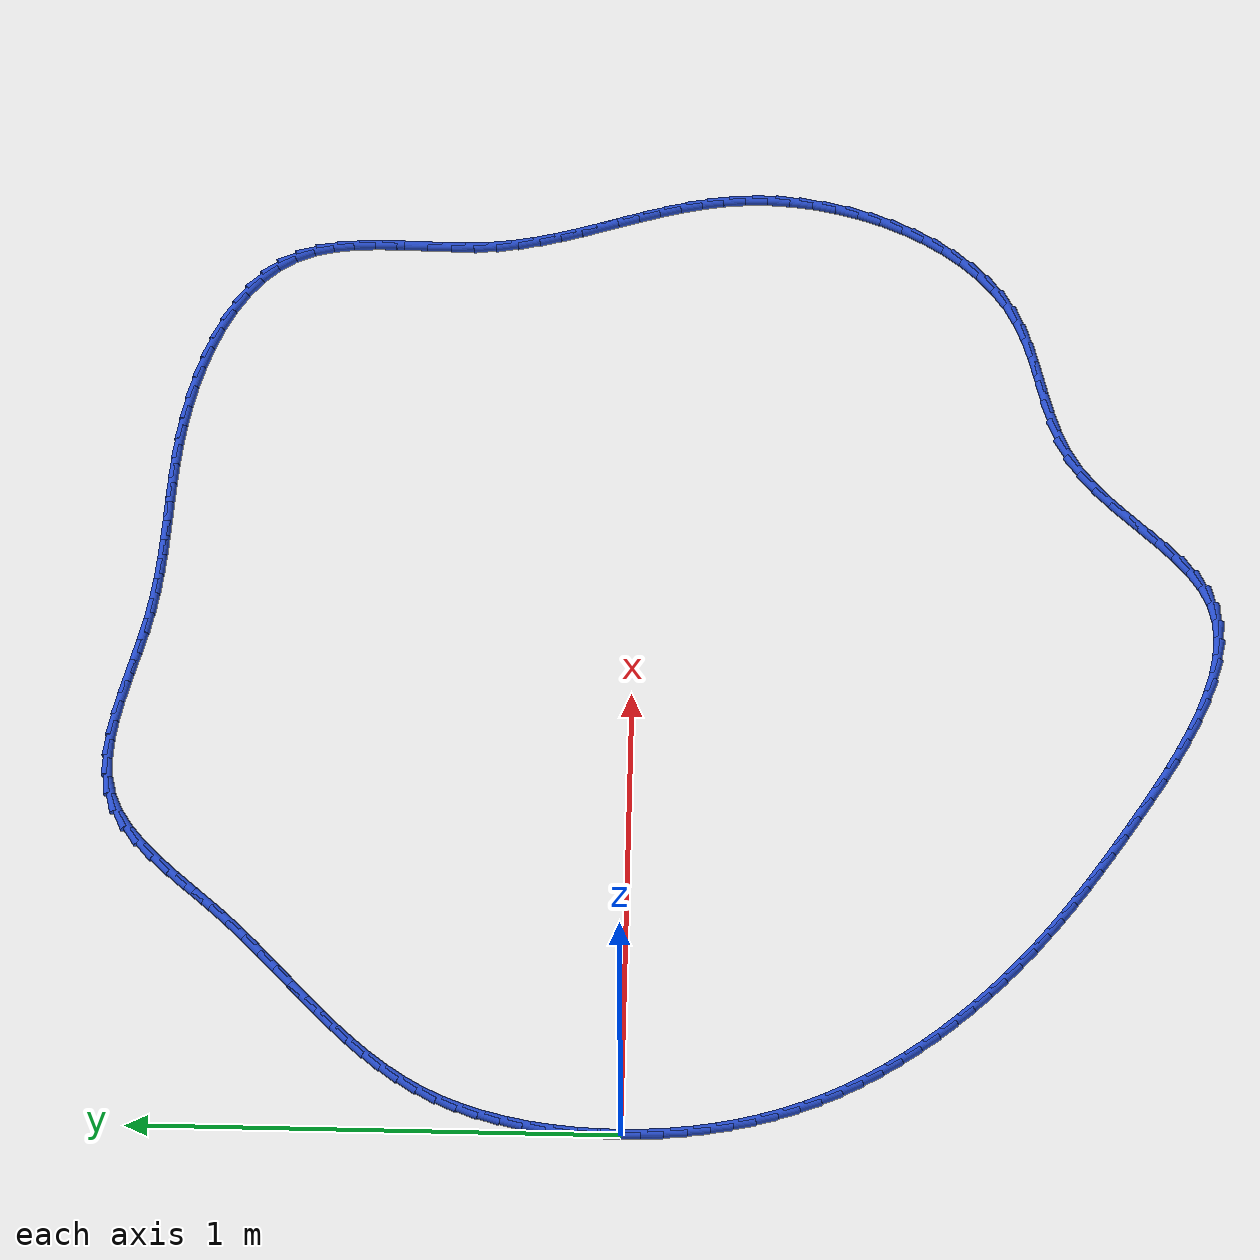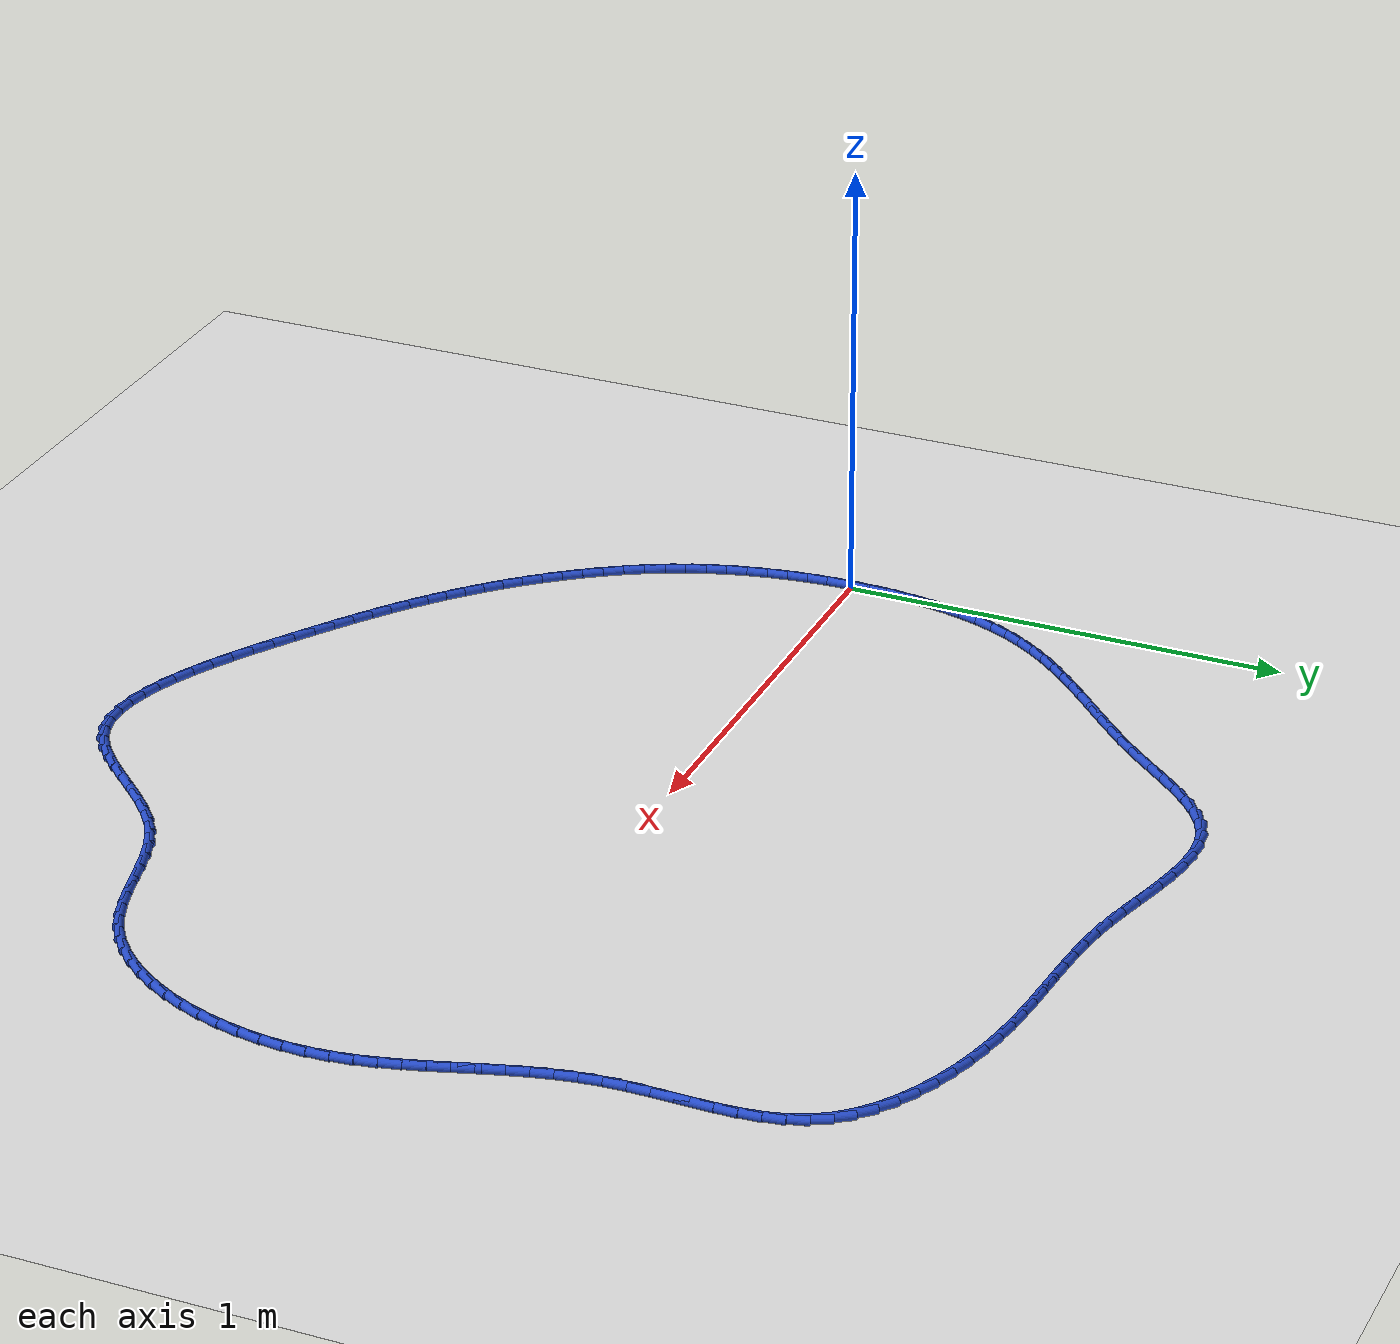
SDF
<sdf version="1.6">
 <world name="default">
  <light name="sun" type="directional">
   <pose>0 0 10 0 -0 0</pose>
   <diffuse>0.8 0.8 0.8 1</diffuse>
   <specular>0.2 0.2 0.2 1</specular>
   <attenuation>
    <range>1000</range>
    <constant>0.9</constant>
    <linear>0.01</linear>
    <quadratic>0.001</quadratic>
   </attenuation>
   <direction>-0.5 0.1 -0.9</direction>
  </light>
  <model name="ground_plane">
   <static>1</static>
   <link name="link">
    <collision name="collision">
     <geometry><plane><normal>0 0 1</normal><size>100 100</size></plane></geometry>
     <surface><friction><ode><mu>100</mu><mu2>50</mu2></ode></friction></surface>
    </collision>
    <visual name="visual">
     <cast_shadows>0</cast_shadows>
     <geometry><plane><normal>0 0 1</normal><size>100 100</size></plane></geometry>
     <material>
      <script><uri>file://media/materials/scripts/gazebo.material</uri><name>Gazebo/WhiteGlow</name></script>
     </material>
    </visual>
   </link>
  </model>
  <gravity>0 0 -9.8</gravity>
  <magnetic_field>6e-06 2.3e-05 -4.2e-05</magnetic_field>
  <atmosphere type="adiabatic"/>
  <physics name="default_physics" default="0" type="ode">
   <max_step_size>0.001</max_step_size>
   <real_time_factor>1</real_time_factor>
   <real_time_update_rate>1000</real_time_update_rate>
  </physics>
  <scene><ambient>0.4 0.4 0.4 1</ambient><background>0.7 0.7 0.7 1</background><shadows>1</shadows></scene>
  <spherical_coordinates>
   <surface_model>EARTH_WGS84</surface_model>
   <latitude_deg>0</latitude_deg>
   <longitude_deg>0</longitude_deg>
   <elevation>0</elevation>
   <heading_deg>0</heading_deg>
  </spherical_coordinates>
  <model name="line">
   <link name="link_0">
    <pose>1.3877787807814457e-17 5.551115123125783e-17 0.01 0 1.57 1.5592415032549907</pose>
    <collision name="collision">
     <geometry><cylinder><radius>0.01</radius><length>0.08</length></cylinder></geometry>
    </collision>
    <visual name="visual">
     <material>
      <script><name>Gazebo/Blue</name><uri>file://media/materials/scripts/gazebo.material</uri></script>
     </material>
     <geometry><cylinder><radius>0.01</radius><length>0.08</length></cylinder></geometry>
    </visual>
   </link>
   <link name="link_1">
    <pose>0.0005506007339790293 0.0476490383056921 0.01 0 1.57 1.5168082034582062</pose>
    <collision name="collision">
     <geometry><cylinder><radius>0.01</radius><length>0.08</length></cylinder></geometry>
    </collision>
    <visual name="visual">
     <material>
      <script><name>Gazebo/Blue</name><uri>file://media/materials/scripts/gazebo.material</uri></script>
     </material>
     <geometry><cylinder><radius>0.01</radius><length>0.08</length></cylinder></geometry>
    </visual>
   </link>
   <link name="link_2">
    <pose>0.0031275486741620968 0.0953344106193341 0.01 0 1.57 1.4718414360372423</pose>
    <collision name="collision">
     <geometry><cylinder><radius>0.01</radius><length>0.08</length></cylinder></geometry>
    </collision>
    <visual name="visual">
     <material>
      <script><name>Gazebo/Blue</name><uri>file://media/materials/scripts/gazebo.material</uri></script>
     </material>
     <geometry><cylinder><radius>0.01</radius><length>0.08</length></cylinder></geometry>
    </visual>
   </link>
   <link name="link_3">
    <pose>0.007838785824267998 0.14278885655521736 0.01 0 1.57 1.4237807907978421</pose>
    <collision name="collision">
     <geometry><cylinder><radius>0.01</radius><length>0.08</length></cylinder></geometry>
    </collision>
    <visual name="visual">
     <material>
      <script><name>Gazebo/Blue</name><uri>file://media/materials/scripts/gazebo.material</uri></script>
     </material>
     <geometry><cylinder><radius>0.01</radius><length>0.08</length></cylinder></geometry>
    </visual>
   </link>
   <link name="link_4">
    <pose>0.01479225418801551 0.18974511572763328 0.01 0 1.57 1.3720380814729647</pose>
    <collision name="collision">
     <geometry><cylinder><radius>0.01</radius><length>0.08</length></cylinder></geometry>
    </collision>
    <visual name="visual">
     <material>
      <script><name>Gazebo/Blue</name><uri>file://media/materials/scripts/gazebo.material</uri></script>
     </material>
     <geometry><cylinder><radius>0.01</radius><length>0.08</length></cylinder></geometry>
    </visual>
   </link>
   <link name="link_5">
    <pose>0.024095895769123413 0.23593592775087305 0.01 0 1.57 1.3159999961972793</pose>
    <collision name="collision">
     <geometry><cylinder><radius>0.01</radius><length>0.08</length></cylinder></geometry>
    </collision>
    <visual name="visual">
     <material>
      <script><name>Gazebo/Blue</name><uri>file://media/materials/scripts/gazebo.material</uri></script>
     </material>
     <geometry><cylinder><radius>0.01</radius><length>0.08</length></cylinder></geometry>
    </visual>
   </link>
   <link name="link_6">
    <pose>0.03585765257131049 0.281094032239228 0.01 0 1.57 1.2550407736091131</pose>
    <collision name="collision">
     <geometry><cylinder><radius>0.01</radius><length>0.08</length></cylinder></geometry>
    </collision>
    <visual name="visual">
     <material>
      <script><name>Gazebo/Blue</name><uri>file://media/materials/scripts/gazebo.material</uri></script>
     </material>
     <geometry><cylinder><radius>0.01</radius><length>0.08</length></cylinder></geometry>
    </visual>
   </link>
   <link name="link_7">
    <pose>0.05018546659829553 0.3249521688069897 0.01 0 1.57 1.1885493299797951</pose>
    <collision name="collision">
     <geometry><cylinder><radius>0.01</radius><length>0.08</length></cylinder></geometry>
    </collision>
    <visual name="visual">
     <material>
      <script><name>Gazebo/Blue</name><uri>file://media/materials/scripts/gazebo.material</uri></script>
     </material>
     <geometry><cylinder><radius>0.01</radius><length>0.08</length></cylinder></geometry>
    </visual>
   </link>
   <link name="link_8">
    <pose>0.0671872798537973 0.36724307706844916 0.01 0 1.57 1.115976135121178</pose>
    <collision name="collision">
     <geometry><cylinder><radius>0.01</radius><length>0.08</length></cylinder></geometry>
    </collision>
    <visual name="visual">
     <material>
      <script><name>Gazebo/Blue</name><uri>file://media/materials/scripts/gazebo.material</uri></script>
     </material>
     <geometry><cylinder><radius>0.01</radius><length>0.08</length></cylinder></geometry>
    </visual>
   </link>
   <link name="link_9">
    <pose>0.08697103334464618 0.40769949801008654 0.01 0 1.57 1.0394892135325797</pose>
    <collision name="collision">
     <geometry><cylinder><radius>0.01</radius><length>0.08</length></cylinder></geometry>
    </collision>
    <visual name="visual">
     <material>
      <script><name>Gazebo/Blue</name><uri>file://media/materials/scripts/gazebo.material</uri></script>
     </material>
     <geometry><cylinder><radius>0.01</radius><length>0.08</length></cylinder></geometry>
    </visual>
   </link>
   <link name="link_10">
    <pose>0.10957082173328837 0.44615582002415427 0.01 0 1.57 0.9691435873972878</pose>
    <collision name="collision">
     <geometry><cylinder><radius>0.01</radius><length>0.08</length></cylinder></geometry>
    </collision>
    <visual name="visual">
     <material>
      <script><name>Gazebo/Blue</name><uri>file://media/materials/scripts/gazebo.material</uri></script>
     </material>
     <geometry><cylinder><radius>0.01</radius><length>0.08</length></cylinder></geometry>
    </visual>
   </link>
   <link name="link_11">
    <pose>0.1347461829364904 0.48282435110296645 0.01 0 1.57 0.9082709454076849</pose>
    <collision name="collision">
     <geometry><cylinder><radius>0.01</radius><length>0.08</length></cylinder></geometry>
    </collision>
    <visual name="visual">
     <material>
      <script><name>Gazebo/Blue</name><uri>file://media/materials/scripts/gazebo.material</uri></script>
     </material>
     <geometry><cylinder><radius>0.01</radius><length>0.08</length></cylinder></geometry>
    </visual>
   </link>
   <link name="link_12">
    <pose>0.16219286048577009 0.5180052104069789 0.01 0 1.57 0.8574978983794502</pose>
    <collision name="collision">
     <geometry><cylinder><radius>0.01</radius><length>0.08</length></cylinder></geometry>
    </collision>
    <visual name="visual">
     <material>
      <script><name>Gazebo/Blue</name><uri>file://media/materials/scripts/gazebo.material</uri></script>
     </material>
     <geometry><cylinder><radius>0.01</radius><length>0.08</length></cylinder></geometry>
    </visual>
   </link>
   <link name="link_13">
    <pose>0.19160659791264525 0.5519985170966474 0.01 0 1.57 0.8170058332884267</pose>
    <collision name="collision">
     <geometry><cylinder><radius>0.01</radius><length>0.08</length></cylinder></geometry>
    </collision>
    <visual name="visual">
     <material>
      <script><name>Gazebo/Blue</name><uri>file://media/materials/scripts/gazebo.material</uri></script>
     </material>
     <geometry><cylinder><radius>0.01</radius><length>0.08</length></cylinder></geometry>
    </visual>
   </link>
   <link name="link_14">
    <pose>0.22268313874863369 0.5851043903324279 0.01 0 1.57 0.786683250902086</pose>
    <collision name="collision">
     <geometry><cylinder><radius>0.01</radius><length>0.08</length></cylinder></geometry>
    </collision>
    <visual name="visual">
     <material>
      <script><name>Gazebo/Blue</name><uri>file://media/materials/scripts/gazebo.material</uri></script>
     </material>
     <geometry><cylinder><radius>0.01</radius><length>0.08</length></cylinder></geometry>
    </visual>
   </link>
   <link name="link_15">
    <pose>0.25511822652525323 0.6176229492747761 0.01 0 1.57 0.7662586834641331</pose>
    <collision name="collision">
     <geometry><cylinder><radius>0.01</radius><length>0.08</length></cylinder></geometry>
    </collision>
    <visual name="visual">
     <material>
      <script><name>Gazebo/Blue</name><uri>file://media/materials/scripts/gazebo.material</uri></script>
     </material>
     <geometry><cylinder><radius>0.01</radius><length>0.08</length></cylinder></geometry>
    </visual>
   </link>
   <link name="link_16">
    <pose>0.2886076047740218 0.6498543130841481 0.01 0 1.57 0.7553979403237775</pose>
    <collision name="collision">
     <geometry><cylinder><radius>0.01</radius><length>0.08</length></cylinder></geometry>
    </collision>
    <visual name="visual">
     <material>
      <script><name>Gazebo/Blue</name><uri>file://media/materials/scripts/gazebo.material</uri></script>
     </material>
     <geometry><cylinder><radius>0.01</radius><length>0.08</length></cylinder></geometry>
    </visual>
   </link>
   <link name="link_17">
    <pose>0.32284701702645713 0.6820986009209995 0.01 0 1.57 0.7537641779279588</pose>
    <collision name="collision">
     <geometry><cylinder><radius>0.01</radius><length>0.08</length></cylinder></geometry>
    </collision>
    <visual name="visual">
     <material>
      <script><name>Gazebo/Blue</name><uri>file://media/materials/scripts/gazebo.material</uri></script>
     </material>
     <geometry><cylinder><radius>0.01</radius><length>0.08</length></cylinder></geometry>
    </visual>
   </link>
   <link name="link_18">
    <pose>0.357532206814077 0.7146559319457862 0.01 0 1.57 0.7610458376176564</pose>
    <collision name="collision">
     <geometry><cylinder><radius>0.01</radius><length>0.08</length></cylinder></geometry>
    </collision>
    <visual name="visual">
     <material>
      <script><name>Gazebo/Blue</name><uri>file://media/materials/scripts/gazebo.material</uri></script>
     </material>
     <geometry><cylinder><radius>0.01</radius><length>0.08</length></cylinder></geometry>
    </visual>
   </link>
   <link name="link_19">
    <pose>0.39235891766839937 0.7478264253189639 0.01 0 1.57 0.7769588065728732</pose>
    <collision name="collision">
     <geometry><cylinder><radius>0.01</radius><length>0.08</length></cylinder></geometry>
    </collision>
    <visual name="visual">
     <material>
      <script><name>Gazebo/Blue</name><uri>file://media/materials/scripts/gazebo.material</uri></script>
     </material>
     <geometry><cylinder><radius>0.01</radius><length>0.08</length></cylinder></geometry>
    </visual>
   </link>
   <link name="link_20">
    <pose>0.42702289312094177 0.7819102002009886 0.01 0 1.57 0.8012282717308266</pose>
    <collision name="collision">
     <geometry><cylinder><radius>0.01</radius><length>0.08</length></cylinder></geometry>
    </collision>
    <visual name="visual">
     <material>
      <script><name>Gazebo/Blue</name><uri>file://media/materials/scripts/gazebo.material</uri></script>
     </material>
     <geometry><cylinder><radius>0.01</radius><length>0.08</length></cylinder></geometry>
    </visual>
   </link>
   <link name="link_21">
    <pose>0.4612198767032226 0.8172073757523164 0.01 0 1.57 0.832322792454036</pose>
    <collision name="collision">
     <geometry><cylinder><radius>0.01</radius><length>0.08</length></cylinder></geometry>
    </collision>
    <visual name="visual">
     <material>
      <script><name>Gazebo/Blue</name><uri>file://media/materials/scripts/gazebo.material</uri></script>
     </material>
     <geometry><cylinder><radius>0.01</radius><length>0.08</length></cylinder></geometry>
    </visual>
   </link>
   <link name="link_22">
    <pose>0.4946744441863599 0.8539587511898754 0.01 0 1.57 0.8526725860245864</pose>
    <collision name="collision">
     <geometry><cylinder><radius>0.01</radius><length>0.08</length></cylinder></geometry>
    </collision>
    <visual name="visual">
     <material>
      <script><name>Gazebo/Blue</name><uri>file://media/materials/scripts/gazebo.material</uri></script>
     </material>
     <geometry><cylinder><radius>0.01</radius><length>0.08</length></cylinder></geometry>
    </visual>
   </link>
   <link name="link_23">
    <pose>0.5275243492765683 0.8915550463709637 0.01 0 1.57 0.8497582648176932</pose>
    <collision name="collision">
     <geometry><cylinder><radius>0.01</radius><length>0.08</length></cylinder></geometry>
    </collision>
    <visual name="visual">
     <material>
      <script><name>Gazebo/Blue</name><uri>file://media/materials/scripts/gazebo.material</uri></script>
     </material>
     <geometry><cylinder><radius>0.01</radius><length>0.08</length></cylinder></geometry>
    </visual>
   </link>
   <link name="link_24">
    <pose>0.5602163338512135 0.9287512635979086 0.01 0 1.57 0.8225589992135482</pose>
    <collision name="collision">
     <geometry><cylinder><radius>0.01</radius><length>0.08</length></cylinder></geometry>
    </collision>
    <visual name="visual">
     <material>
      <script><name>Gazebo/Blue</name><uri>file://media/materials/scripts/gazebo.material</uri></script>
     </material>
     <geometry><cylinder><radius>0.01</radius><length>0.08</length></cylinder></geometry>
    </visual>
   </link>
   <link name="link_25">
    <pose>0.5932045809711561 0.9642870955546824 0.01 0 1.57 0.7684670238173941</pose>
    <collision name="collision">
     <geometry><cylinder><radius>0.01</radius><length>0.08</length></cylinder></geometry>
    </collision>
    <visual name="visual">
     <material>
      <script><name>Gazebo/Blue</name><uri>file://media/materials/scripts/gazebo.material</uri></script>
     </material>
     <geometry><cylinder><radius>0.01</radius><length>0.08</length></cylinder></geometry>
    </visual>
   </link>
   <link name="link_26">
    <pose>0.6269432736972561 0.9969022349252559 0.01 0 1.57 0.6830520195893657</pose>
    <collision name="collision">
     <geometry><cylinder><radius>0.01</radius><length>0.08</length></cylinder></geometry>
    </collision>
    <visual name="visual">
     <material>
      <script><name>Gazebo/Blue</name><uri>file://media/materials/scripts/gazebo.material</uri></script>
     </material>
     <geometry><cylinder><radius>0.01</radius><length>0.08</length></cylinder></geometry>
    </visual>
   </link>
   <link name="link_27">
    <pose>0.6618865950903736 1.0253363743936013 0.01 0 1.57 0.5608848319711809</pose>
    <collision name="collision">
     <geometry><cylinder><radius>0.01</radius><length>0.08</length></cylinder></geometry>
    </collision>
    <visual name="visual">
     <material>
      <script><name>Gazebo/Blue</name><uri>file://media/materials/scripts/gazebo.material</uri></script>
     </material>
     <geometry><cylinder><radius>0.01</radius><length>0.08</length></cylinder></geometry>
    </visual>
   </link>
   <link name="link_28">
    <pose>0.6984887282113688 1.04832920664369 0.01 0 1.57 0.3983347546345636</pose>
    <collision name="collision">
     <geometry><cylinder><radius>0.01</radius><length>0.08</length></cylinder></geometry>
    </collision>
    <visual name="visual">
     <material>
      <script><name>Gazebo/Blue</name><uri>file://media/materials/scripts/gazebo.material</uri></script>
     </material>
     <geometry><cylinder><radius>0.01</radius><length>0.08</length></cylinder></geometry>
    </visual>
   </link>
   <link name="link_29">
    <pose>0.7372034574226284 1.0646215913000199 0.01 0 1.57 0.21392442425331024</pose>
    <collision name="collision">
     <geometry><cylinder><radius>0.01</radius><length>0.08</length></cylinder></geometry>
    </collision>
    <visual name="visual">
     <material>
      <script><name>Gazebo/Blue</name><uri>file://media/materials/scripts/gazebo.material</uri></script>
     </material>
     <geometry><cylinder><radius>0.01</radius><length>0.08</length></cylinder></geometry>
    </visual>
   </link>
   <link name="link_30">
    <pose>0.7782824544752611 1.073545946301163 0.01 0 1.57 0.056478903532812944</pose>
    <collision name="collision">
     <geometry><cylinder><radius>0.01</radius><length>0.08</length></cylinder></geometry>
    </collision>
    <visual name="visual">
     <material>
      <script><name>Gazebo/Blue</name><uri>file://media/materials/scripts/gazebo.material</uri></script>
     </material>
     <geometry><cylinder><radius>0.01</radius><length>0.08</length></cylinder></geometry>
    </visual>
   </link>
   <link name="link_31">
    <pose>0.8214472178749941 1.075986440311302 0.01 0 1.57 -0.06469218494856696</pose>
    <collision name="collision">
     <geometry><cylinder><radius>0.01</radius><length>0.08</length></cylinder></geometry>
    </collision>
    <visual name="visual">
     <material>
      <script><name>Gazebo/Blue</name><uri>file://media/materials/scripts/gazebo.material</uri></script>
     </material>
     <geometry><cylinder><radius>0.01</radius><length>0.08</length></cylinder></geometry>
    </visual>
   </link>
   <link name="link_32">
    <pose>0.8663333669465786 1.0730785996075394 0.01 0 1.57 -0.15278278693164793</pose>
    <collision name="collision">
     <geometry><cylinder><radius>0.01</radius><length>0.08</length></cylinder></geometry>
    </collision>
    <visual name="visual">
     <material>
      <script><name>Gazebo/Blue</name><uri>file://media/materials/scripts/gazebo.material</uri></script>
     </material>
     <geometry><cylinder><radius>0.01</radius><length>0.08</length></cylinder></geometry>
    </visual>
   </link>
   <link name="link_33">
    <pose>0.9125765210147673 1.0659579504669805 0.01 0 1.57 -0.2126307090838199</pose>
    <collision name="collision">
     <geometry><cylinder><radius>0.01</radius><length>0.08</length></cylinder></geometry>
    </collision>
    <visual name="visual">
     <material>
      <script><name>Gazebo/Blue</name><uri>file://media/materials/scripts/gazebo.material</uri></script>
     </material>
     <geometry><cylinder><radius>0.01</radius><length>0.08</length></cylinder></geometry>
    </visual>
   </link>
   <link name="link_34">
    <pose>0.9598122994043109 1.0557600191667267 0.01 0 1.57 -0.24839093432079754</pose>
    <collision name="collision">
     <geometry><cylinder><radius>0.01</radius><length>0.08</length></cylinder></geometry>
    </collision>
    <visual name="visual">
     <material>
      <script><name>Gazebo/Blue</name><uri>file://media/materials/scripts/gazebo.material</uri></script>
     </material>
     <geometry><cylinder><radius>0.01</radius><length>0.08</length></cylinder></geometry>
    </visual>
   </link>
   <link name="link_35">
    <pose>1.0076763214399618 1.043620331983883 0.01 0 1.57 -0.2627701634435653</pose>
    <collision name="collision">
     <geometry><cylinder><radius>0.01</radius><length>0.08</length></cylinder></geometry>
    </collision>
    <visual name="visual">
     <material>
      <script><name>Gazebo/Blue</name><uri>file://media/materials/scripts/gazebo.material</uri></script>
     </material>
     <geometry><cylinder><radius>0.01</radius><length>0.08</length></cylinder></geometry>
    </visual>
   </link>
   <link name="link_36">
    <pose>1.0558042064464714 1.0306744151955518 0.01 0 1.57 -0.2568921313939172</pose>
    <collision name="collision">
     <geometry><cylinder><radius>0.01</radius><length>0.08</length></cylinder></geometry>
    </collision>
    <visual name="visual">
     <material>
      <script><name>Gazebo/Blue</name><uri>file://media/materials/scripts/gazebo.material</uri></script>
     </material>
     <geometry><cylinder><radius>0.01</radius><length>0.08</length></cylinder></geometry>
    </visual>
   </link>
   <link name="link_37">
    <pose>1.103831573748591 1.018057795078837 0.01 0 1.57 -0.23030615255588396</pose>
    <collision name="collision">
     <geometry><cylinder><radius>0.01</radius><length>0.08</length></cylinder></geometry>
    </collision>
    <visual name="visual">
     <material>
      <script><name>Gazebo/Blue</name><uri>file://media/materials/scripts/gazebo.material</uri></script>
     </material>
     <geometry><cylinder><radius>0.01</radius><length>0.08</length></cylinder></geometry>
    </visual>
   </link>
   <link name="link_38">
    <pose>1.1513940426710734 1.0069059979108423 0.01 0 1.57 -0.18613990437667244</pose>
    <collision name="collision">
     <geometry><cylinder><radius>0.01</radius><length>0.08</length></cylinder></geometry>
    </collision>
    <visual name="visual">
     <material>
      <script><name>Gazebo/Blue</name><uri>file://media/materials/scripts/gazebo.material</uri></script>
     </material>
     <geometry><cylinder><radius>0.01</radius><length>0.08</length></cylinder></geometry>
    </visual>
   </link>
   <link name="link_39">
    <pose>1.1982154441939137 0.9980885953943709 0.01 0 1.57 -0.1439422692745107</pose>
    <collision name="collision">
     <geometry><cylinder><radius>0.01</radius><length>0.08</length></cylinder></geometry>
    </collision>
    <visual name="visual">
     <material>
      <script><name>Gazebo/Blue</name><uri>file://media/materials/scripts/gazebo.material</uri></script>
     </material>
     <geometry><cylinder><radius>0.01</radius><length>0.08</length></cylinder></geometry>
    </visual>
   </link>
   <link name="link_40">
    <pose>1.2443769716416897 0.9913977262109258 0.01 0 1.57 -0.11001241365971014</pose>
    <collision name="collision">
     <geometry><cylinder><radius>0.01</radius><length>0.08</length></cylinder></geometry>
    </collision>
    <visual name="visual">
     <material>
      <script><name>Gazebo/Blue</name><uri>file://media/materials/scripts/gazebo.material</uri></script>
     </material>
     <geometry><cylinder><radius>0.01</radius><length>0.08</length></cylinder></geometry>
    </visual>
   </link>
   <link name="link_41">
    <pose>1.2900503022665246 0.986352723658589 0.01 0 1.57 -0.08533186122812078</pose>
    <collision name="collision">
     <geometry><cylinder><radius>0.01</radius><length>0.08</length></cylinder></geometry>
    </collision>
    <visual name="visual">
     <material>
      <script><name>Gazebo/Blue</name><uri>file://media/materials/scripts/gazebo.material</uri></script>
     </material>
     <geometry><cylinder><radius>0.01</radius><length>0.08</length></cylinder></geometry>
    </visual>
   </link>
   <link name="link_42">
    <pose>1.3354071133273442 0.9824729210149266 0.01 0 1.57 -0.07055577632179359</pose>
    <collision name="collision">
     <geometry><cylinder><radius>0.01</radius><length>0.08</length></cylinder></geometry>
    </collision>
    <visual name="visual">
     <material>
      <script><name>Gazebo/Blue</name><uri>file://media/materials/scripts/gazebo.material</uri></script>
     </material>
     <geometry><cylinder><radius>0.01</radius><length>0.08</length></cylinder></geometry>
    </visual>
   </link>
   <link name="link_43">
    <pose>1.380619082083077 0.9792776515575038 0.01 0 1.57 -0.06602859057947813</pose>
    <collision name="collision">
     <geometry><cylinder><radius>0.01</radius><length>0.08</length></cylinder></geometry>
    </collision>
    <visual name="visual">
     <material>
      <script><name>Gazebo/Blue</name><uri>file://media/materials/scripts/gazebo.material</uri></script>
     </material>
     <geometry><cylinder><radius>0.01</radius><length>0.08</length></cylinder></geometry>
    </visual>
   </link>
   <link name="link_44">
    <pose>1.4258578857926496 0.9762862485638863 0.01 0 1.57 -0.07180407760694231</pose>
    <collision name="collision">
     <geometry><cylinder><radius>0.01</radius><length>0.08</length></cylinder></geometry>
    </collision>
    <visual name="visual">
     <material>
      <script><name>Gazebo/Blue</name><uri>file://media/materials/scripts/gazebo.material</uri></script>
     </material>
     <geometry><cylinder><radius>0.01</radius><length>0.08</length></cylinder></geometry>
    </visual>
   </link>
   <link name="link_45">
    <pose>1.4712952017149905 0.9730180453116405 0.01 0 1.57 -0.08765712379779685</pose>
    <collision name="collision">
     <geometry><cylinder><radius>0.01</radius><length>0.08</length></cylinder></geometry>
    </collision>
    <visual name="visual">
     <material>
      <script><name>Gazebo/Blue</name><uri>file://media/materials/scripts/gazebo.material</uri></script>
     </material>
     <geometry><cylinder><radius>0.01</radius><length>0.08</length></cylinder></geometry>
    </visual>
   </link>
   <link name="link_46">
    <pose>1.5171027071090248 0.9689923750783316 0.01 0 1.57 -0.11308345581966468</pose>
    <collision name="collision">
     <geometry><cylinder><radius>0.01</radius><length>0.08</length></cylinder></geometry>
    </collision>
    <visual name="visual">
     <material>
      <script><name>Gazebo/Blue</name><uri>file://media/materials/scripts/gazebo.material</uri></script>
     </material>
     <geometry><cylinder><radius>0.01</radius><length>0.08</length></cylinder></geometry>
    </visual>
   </link>
   <link name="link_47">
    <pose>1.5634520792336812 0.9637285711415254 0.01 0 1.57 -0.14729293037486305</pose>
    <collision name="collision">
     <geometry><cylinder><radius>0.01</radius><length>0.08</length></cylinder></geometry>
    </collision>
    <visual name="visual">
     <material>
      <script><name>Gazebo/Blue</name><uri>file://media/materials/scripts/gazebo.material</uri></script>
     </material>
     <geometry><cylinder><radius>0.01</radius><length>0.08</length></cylinder></geometry>
    </visual>
   </link>
   <link name="link_48">
    <pose>1.6105149953478866 0.9567459667787876 0.01 0 1.57 -0.18918848437810185</pose>
    <collision name="collision">
     <geometry><cylinder><radius>0.01</radius><length>0.08</length></cylinder></geometry>
    </collision>
    <visual name="visual">
     <material>
      <script><name>Gazebo/Blue</name><uri>file://media/materials/scripts/gazebo.material</uri></script>
     </material>
     <geometry><cylinder><radius>0.01</radius><length>0.08</length></cylinder></geometry>
    </visual>
   </link>
   <link name="link_49">
    <pose>1.658457001704698 0.9475661063060195 0.01 0 1.57 -0.2365714419183578</pose>
    <collision name="collision">
     <geometry><cylinder><radius>0.01</radius><length>0.08</length></cylinder></geometry>
    </collision>
    <visual name="visual">
     <material>
      <script><name>Gazebo/Blue</name><uri>file://media/materials/scripts/gazebo.material</uri></script>
     </material>
     <geometry><cylinder><radius>0.01</radius><length>0.08</length></cylinder></geometry>
    </visual>
   </link>
   <link name="link_50">
    <pose>1.7070623224504706 0.9358480510818011 0.01 0 1.57 -0.2885197519070699</pose>
    <collision name="collision">
     <geometry><cylinder><radius>0.01</radius><length>0.08</length></cylinder></geometry>
    </collision>
    <visual name="visual">
     <material>
      <script><name>Gazebo/Blue</name><uri>file://media/materials/scripts/gazebo.material</uri></script>
     </material>
     <geometry><cylinder><radius>0.01</radius><length>0.08</length></cylinder></geometry>
    </visual>
   </link>
   <link name="link_51">
    <pose>1.755516259196805 0.9214668532355754 0.01 0 1.57 -0.3469289847563097</pose>
    <collision name="collision">
     <geometry><cylinder><radius>0.01</radius><length>0.08</length></cylinder></geometry>
    </collision>
    <visual name="visual">
     <material>
      <script><name>Gazebo/Blue</name><uri>file://media/materials/scripts/gazebo.material</uri></script>
     </material>
     <geometry><cylinder><radius>0.01</radius><length>0.08</length></cylinder></geometry>
    </visual>
   </link>
   <link name="link_52">
    <pose>1.802951662016576 0.9043164806123 0.01 0 1.57 -0.41420708618827373</pose>
    <collision name="collision">
     <geometry><cylinder><radius>0.01</radius><length>0.08</length></cylinder></geometry>
    </collision>
    <visual name="visual">
     <material>
      <script><name>Gazebo/Blue</name><uri>file://media/materials/scripts/gazebo.material</uri></script>
     </material>
     <geometry><cylinder><radius>0.01</radius><length>0.08</length></cylinder></geometry>
    </visual>
   </link>
   <link name="link_53">
    <pose>1.8485013809826565 0.8842909010569322 0.01 0 1.57 -0.4932589756532916</pose>
    <collision name="collision">
     <geometry><cylinder><radius>0.01</radius><length>0.08</length></cylinder></geometry>
    </collision>
    <visual name="visual">
     <material>
      <script><name>Gazebo/Blue</name><uri>file://media/materials/scripts/gazebo.material</uri></script>
     </material>
     <geometry><cylinder><radius>0.01</radius><length>0.08</length></cylinder></geometry>
    </visual>
   </link>
   <link name="link_54">
    <pose>1.8912982661679218 0.8612840824144296 0.01 0 1.57 -0.5875811224807701</pose>
    <collision name="collision">
     <geometry><cylinder><radius>0.01</radius><length>0.08</length></cylinder></geometry>
    </collision>
    <visual name="visual">
     <material>
      <script><name>Gazebo/Blue</name><uri>file://media/materials/scripts/gazebo.material</uri></script>
     </material>
     <geometry><cylinder><radius>0.01</radius><length>0.08</length></cylinder></geometry>
    </visual>
   </link>
   <link name="link_55">
    <pose>1.9304751676452439 0.8351899925297498 0.01 0 1.57 -0.7011557776033039</pose>
    <collision name="collision">
     <geometry><cylinder><radius>0.01</radius><length>0.08</length></cylinder></geometry>
    </collision>
    <visual name="visual">
     <material>
      <script><name>Gazebo/Blue</name><uri>file://media/materials/scripts/gazebo.material</uri></script>
     </material>
     <geometry><cylinder><radius>0.01</radius><length>0.08</length></cylinder></geometry>
    </visual>
   </link>
   <link name="link_56">
    <pose>1.9651649354874985 0.8059025992478506 0.01 0 1.57 -0.8378552969285713</pose>
    <collision name="collision">
     <geometry><cylinder><radius>0.01</radius><length>0.08</length></cylinder></geometry>
    </collision>
    <visual name="visual">
     <material>
      <script><name>Gazebo/Blue</name><uri>file://media/materials/scripts/gazebo.material</uri></script>
     </material>
     <geometry><cylinder><radius>0.01</radius><length>0.08</length></cylinder></geometry>
    </visual>
   </link>
   <link name="link_57">
    <pose>1.994500419767558 0.7733158704136892 0.01 0 1.57 -0.9999236391090426</pose>
    <collision name="collision">
     <geometry><cylinder><radius>0.01</radius><length>0.08</length></cylinder></geometry>
    </collision>
    <visual name="visual">
     <material>
      <script><name>Gazebo/Blue</name><uri>file://media/materials/scripts/gazebo.material</uri></script>
     </material>
     <geometry><cylinder><radius>0.01</radius><length>0.08</length></cylinder></geometry>
    </visual>
   </link>
   <link name="link_58">
    <pose>2.0176145457716563 0.7373237974003014 0.01 0 1.57 -1.1755204792320735</pose>
    <collision name="collision">
     <geometry><cylinder><radius>0.01</radius><length>0.08</length></cylinder></geometry>
    </collision>
    <visual name="visual">
     <material>
      <script><name>Gazebo/Blue</name><uri>file://media/materials/scripts/gazebo.material</uri></script>
     </material>
     <geometry><cylinder><radius>0.01</radius><length>0.08</length></cylinder></geometry>
    </visual>
   </link>
   <link name="link_59">
    <pose>2.0340440755863485 0.6979466989244446 0.01 0 1.57 -1.3247147613998327</pose>
    <collision name="collision">
     <geometry><cylinder><radius>0.01</radius><length>0.08</length></cylinder></geometry>
    </collision>
    <visual name="visual">
     <material>
      <script><name>Gazebo/Blue</name><uri>file://media/materials/scripts/gazebo.material</uri></script>
     </material>
     <geometry><cylinder><radius>0.01</radius><length>0.08</length></cylinder></geometry>
    </visual>
   </link>
   <link name="link_60">
    <pose>2.0446737173733105 0.6556265552429148 0.01 0 1.57 -1.437565747576375</pose>
    <collision name="collision">
     <geometry><cylinder><radius>0.01</radius><length>0.08</length></cylinder></geometry>
    </collision>
    <visual name="visual">
     <material>
      <script><name>Gazebo/Blue</name><uri>file://media/materials/scripts/gazebo.material</uri></script>
     </material>
     <geometry><cylinder><radius>0.01</radius><length>0.08</length></cylinder></geometry>
    </visual>
   </link>
   <link name="link_61">
    <pose>2.0506690812311787 0.6108932177414257 0.01 0 1.57 -1.516647767356623</pose>
    <collision name="collision">
     <geometry><cylinder><radius>0.01</radius><length>0.08</length></cylinder></geometry>
    </collision>
    <visual name="visual">
     <material>
      <script><name>Gazebo/Blue</name><uri>file://media/materials/scripts/gazebo.material</uri></script>
     </material>
     <geometry><cylinder><radius>0.01</radius><length>0.08</length></cylinder></geometry>
    </visual>
   </link>
   <link name="link_62">
    <pose>2.053195777258591 0.5642765378056899 0.01 0 1.57 -1.5661343322511034</pose>
    <collision name="collision">
     <geometry><cylinder><radius>0.01</radius><length>0.08</length></cylinder></geometry>
    </collision>
    <visual name="visual">
     <material>
      <script><name>Gazebo/Blue</name><uri>file://media/materials/scripts/gazebo.material</uri></script>
     </material>
     <geometry><cylinder><radius>0.01</radius><length>0.08</length></cylinder></geometry>
    </visual>
   </link>
   <link name="link_63">
    <pose>2.053419415554186 0.5163063668214218 0.01 0 1.57 1.5520705393982241</pose>
    <collision name="collision">
     <geometry><cylinder><radius>0.01</radius><length>0.08</length></cylinder></geometry>
    </collision>
    <visual name="visual">
     <material>
      <script><name>Gazebo/Blue</name><uri>file://media/materials/scripts/gazebo.material</uri></script>
     </material>
     <geometry><cylinder><radius>0.01</radius><length>0.08</length></cylinder></geometry>
    </visual>
   </link>
   <link name="link_64">
    <pose>2.052505606216599 0.4675125561743343 0.01 0 1.57 1.5527561127341483</pose>
    <collision name="collision">
     <geometry><cylinder><radius>0.01</radius><length>0.08</length></cylinder></geometry>
    </collision>
    <visual name="visual">
     <material>
      <script><name>Gazebo/Blue</name><uri>file://media/materials/scripts/gazebo.material</uri></script>
     </material>
     <geometry><cylinder><radius>0.01</radius><length>0.08</length></cylinder></geometry>
    </visual>
   </link>
   <link name="link_65">
    <pose>2.051619959344469 0.4184249572501405 0.01 0 1.57 -1.564489020364419</pose>
    <collision name="collision">
     <geometry><cylinder><radius>0.01</radius><length>0.08</length></cylinder></geometry>
    </collision>
    <visual name="visual">
     <material>
      <script><name>Gazebo/Blue</name><uri>file://media/materials/scripts/gazebo.material</uri></script>
     </material>
     <geometry><cylinder><radius>0.01</radius><length>0.08</length></cylinder></geometry>
    </visual>
   </link>
   <link name="link_66">
    <pose>2.051928085036432 0.3695734214345538 0.01 0 1.57 -1.5153809063706811</pose>
    <collision name="collision">
     <geometry><cylinder><radius>0.01</radius><length>0.08</length></cylinder></geometry>
    </collision>
    <visual name="visual">
     <material>
      <script><name>Gazebo/Blue</name><uri>file://media/materials/scripts/gazebo.material</uri></script>
     </material>
     <geometry><cylinder><radius>0.01</radius><length>0.08</length></cylinder></geometry>
    </visual>
   </link>
   <link name="link_67">
    <pose>2.0545955030594105 0.3214877620070763 0.01 0 1.57 -1.4470990301535427</pose>
    <collision name="collision">
     <geometry><cylinder><radius>0.01</radius><length>0.08</length></cylinder></geometry>
    </collision>
    <visual name="visual">
     <material>
      <script><name>Gazebo/Blue</name><uri>file://media/materials/scripts/gazebo.material</uri></script>
     </material>
     <geometry><cylinder><radius>0.01</radius><length>0.08</length></cylinder></geometry>
    </visual>
   </link>
   <link name="link_68">
    <pose>2.0604316724348934 0.27454758890243075 0.01 0 1.57 -1.3845447869739942</pose>
    <collision name="collision">
     <geometry><cylinder><radius>0.01</radius><length>0.08</length></cylinder></geometry>
    </collision>
    <visual name="visual">
     <material>
      <script><name>Gazebo/Blue</name><uri>file://media/materials/scripts/gazebo.material</uri></script>
     </material>
     <geometry><cylinder><radius>0.01</radius><length>0.08</length></cylinder></geometry>
    </visual>
   </link>
   <link name="link_69">
    <pose>2.069082016290396 0.22864146639259056 0.01 0 1.57 -1.334153475552588</pose>
    <collision name="collision">
     <geometry><cylinder><radius>0.01</radius><length>0.08</length></cylinder></geometry>
    </collision>
    <visual name="visual">
     <material>
      <script><name>Gazebo/Blue</name><uri>file://media/materials/scripts/gazebo.material</uri></script>
     </material>
     <geometry><cylinder><radius>0.01</radius><length>0.08</length></cylinder></geometry>
    </visual>
   </link>
   <link name="link_70">
    <pose>2.079954463682541 0.18355777246314128 0.01 0 1.57 -1.2967438928959178</pose>
    <collision name="collision">
     <geometry><cylinder><radius>0.01</radius><length>0.08</length></cylinder></geometry>
    </collision>
    <visual name="visual">
     <material>
      <script><name>Gazebo/Blue</name><uri>file://media/materials/scripts/gazebo.material</uri></script>
     </material>
     <geometry><cylinder><radius>0.01</radius><length>0.08</length></cylinder></geometry>
    </visual>
   </link>
   <link name="link_71">
    <pose>2.092456943667953 0.13908488509966796 0.01 0 1.57 -1.2727264518706305</pose>
    <collision name="collision">
     <geometry><cylinder><radius>0.01</radius><length>0.08</length></cylinder></geometry>
    </collision>
    <visual name="visual">
     <material>
      <script><name>Gazebo/Blue</name><uri>file://media/materials/scripts/gazebo.material</uri></script>
     </material>
     <geometry><cylinder><radius>0.01</radius><length>0.08</length></cylinder></geometry>
    </visual>
   </link>
   <link name="link_72">
    <pose>2.1059973853032523 0.09501118228775697 0.01 0 1.57 -1.2622768071640826</pose>
    <collision name="collision">
     <geometry><cylinder><radius>0.01</radius><length>0.08</length></cylinder></geometry>
    </collision>
    <visual name="visual">
     <material>
      <script><name>Gazebo/Blue</name><uri>file://media/materials/scripts/gazebo.material</uri></script>
     </material>
     <geometry><cylinder><radius>0.01</radius><length>0.08</length></cylinder></geometry>
    </visual>
   </link>
   <link name="link_73">
    <pose>2.1199837176450647 0.05112504201299341 0.01 0 1.57 -1.2654606687503125</pose>
    <collision name="collision">
     <geometry><cylinder><radius>0.01</radius><length>0.08</length></cylinder></geometry>
    </collision>
    <visual name="visual">
     <material>
      <script><name>Gazebo/Blue</name><uri>file://media/materials/scripts/gazebo.material</uri></script>
     </material>
     <geometry><cylinder><radius>0.01</radius><length>0.08</length></cylinder></geometry>
    </visual>
   </link>
   <link name="link_74">
    <pose>2.1338238697500116 0.0072148422609626985 0.01 0 1.57 -1.282290312422035</pose>
    <collision name="collision">
     <geometry><cylinder><radius>0.01</radius><length>0.08</length></cylinder></geometry>
    </collision>
    <visual name="visual">
     <material>
      <script><name>Gazebo/Blue</name><uri>file://media/materials/scripts/gazebo.material</uri></script>
     </material>
     <geometry><cylinder><radius>0.01</radius><length>0.08</length></cylinder></geometry>
    </visual>
   </link>
   <link name="link_75">
    <pose>2.1469257706747173 -0.03693103898274958 0.01 0 1.57 -1.3127066350233874</pose>
    <collision name="collision">
     <geometry><cylinder><radius>0.01</radius><length>0.08</length></cylinder></geometry>
    </collision>
    <visual name="visual">
     <material>
      <script><name>Gazebo/Blue</name><uri>file://media/materials/scripts/gazebo.material</uri></script>
     </material>
     <geometry><cylinder><radius>0.01</radius><length>0.08</length></cylinder></geometry>
    </visual>
   </link>
   <link name="link_76">
    <pose>2.158697349475804 -0.08152422373255834 0.01 0 1.57 -1.3564872859065393</pose>
    <collision name="collision">
     <geometry><cylinder><radius>0.01</radius><length>0.08</length></cylinder></geometry>
    </collision>
    <visual name="visual">
     <material>
      <script><name>Gazebo/Blue</name><uri>file://media/materials/scripts/gazebo.material</uri></script>
     </material>
     <geometry><cylinder><radius>0.01</radius><length>0.08</length></cylinder></geometry>
    </visual>
   </link>
   <link name="link_77">
    <pose>2.1685465352098947 -0.12677633400287774 0.01 0 1.57 -1.4130904748997954</pose>
    <collision name="collision">
     <geometry><cylinder><radius>0.01</radius><length>0.08</length></cylinder></geometry>
    </collision>
    <visual name="visual">
     <material>
      <script><name>Gazebo/Blue</name><uri>file://media/materials/scripts/gazebo.material</uri></script>
     </material>
     <geometry><cylinder><radius>0.01</radius><length>0.08</length></cylinder></geometry>
    </visual>
   </link>
   <link name="link_78">
    <pose>2.1758812569336135 -0.17289899180812152 0.01 0 1.57 -1.4814618211454147</pose>
    <collision name="collision">
     <geometry><cylinder><radius>0.01</radius><length>0.08</length></cylinder></geometry>
    </collision>
    <visual name="visual">
     <material>
      <script><name>Gazebo/Blue</name><uri>file://media/materials/scripts/gazebo.material</uri></script>
     </material>
     <geometry><cylinder><radius>0.01</radius><length>0.08</length></cylinder></geometry>
    </visual>
   </link>
   <link name="link_79">
    <pose>2.1801095236306853 -0.2201037372347708 0.01 0 1.57 -1.5568854090320874</pose>
    <collision name="collision">
     <geometry><cylinder><radius>0.01</radius><length>0.08</length></cylinder></geometry>
    </collision>
    <visual name="visual">
     <material>
      <script><name>Gazebo/Blue</name><uri>file://media/materials/scripts/gazebo.material</uri></script>
     </material>
     <geometry><cylinder><radius>0.01</radius><length>0.08</length></cylinder></geometry>
    </visual>
   </link>
   <link name="link_80">
    <pose>2.1807821870841124 -0.26845569175613304 0.01 0 1.57 1.5119288705914413</pose>
    <collision name="collision">
     <geometry><cylinder><radius>0.01</radius><length>0.08</length></cylinder></geometry>
    </collision>
    <visual name="visual">
     <material>
      <script><name>Gazebo/Blue</name><uri>file://media/materials/scripts/gazebo.material</uri></script>
     </material>
     <geometry><cylinder><radius>0.01</radius><length>0.08</length></cylinder></geometry>
    </visual>
   </link>
   <link name="link_81">
    <pose>2.177887513269734 -0.3175716127710212 0.01 0 1.57 1.4421809560744194</pose>
    <collision name="collision">
     <geometry><cylinder><radius>0.01</radius><length>0.08</length></cylinder></geometry>
    </collision>
    <visual name="visual">
     <material>
      <script><name>Gazebo/Blue</name><uri>file://media/materials/scripts/gazebo.material</uri></script>
     </material>
     <geometry><cylinder><radius>0.01</radius><length>0.08</length></cylinder></geometry>
    </visual>
   </link>
   <link name="link_82">
    <pose>2.171497209565089 -0.3669827274703546 0.01 0 1.57 1.3740507795493337</pose>
    <collision name="collision">
     <geometry><cylinder><radius>0.01</radius><length>0.08</length></cylinder></geometry>
    </collision>
    <visual name="visual">
     <material>
      <script><name>Gazebo/Blue</name><uri>file://media/materials/scripts/gazebo.material</uri></script>
     </material>
     <geometry><cylinder><radius>0.01</radius><length>0.08</length></cylinder></geometry>
    </visual>
   </link>
   <link name="link_83">
    <pose>2.1616829833477142 -0.4162202630450522 0.01 0 1.57 1.3062073753613277</pose>
    <collision name="collision">
     <geometry><cylinder><radius>0.01</radius><length>0.08</length></cylinder></geometry>
    </collision>
    <visual name="visual">
     <material>
      <script><name>Gazebo/Blue</name><uri>file://media/materials/scripts/gazebo.material</uri></script>
     </material>
     <geometry><cylinder><radius>0.01</radius><length>0.08</length></cylinder></geometry>
    </visual>
   </link>
   <link name="link_84">
    <pose>2.1485165419951495 -0.4648154466860362 0.01 0 1.57 1.2373609760402897</pose>
    <collision name="collision">
     <geometry><cylinder><radius>0.01</radius><length>0.08</length></cylinder></geometry>
    </collision>
    <visual name="visual">
     <material>
      <script><name>Gazebo/Blue</name><uri>file://media/materials/scripts/gazebo.material</uri></script>
     </material>
     <geometry><cylinder><radius>0.01</radius><length>0.08</length></cylinder></geometry>
    </visual>
   </link>
   <link name="link_85">
    <pose>2.1320695928849327 -0.5122995055842243 0.01 0 1.57 1.1662259677164022</pose>
    <collision name="collision">
     <geometry><cylinder><radius>0.01</radius><length>0.08</length></cylinder></geometry>
    </collision>
    <visual name="visual">
     <material>
      <script><name>Gazebo/Blue</name><uri>file://media/materials/scripts/gazebo.material</uri></script>
     </material>
     <geometry><cylinder><radius>0.01</radius><length>0.08</length></cylinder></geometry>
    </visual>
   </link>
   <link name="link_86">
    <pose>2.1124138433946027 -0.5582036669305385 0.01 0 1.57 1.091492674729954</pose>
    <collision name="collision">
     <geometry><cylinder><radius>0.01</radius><length>0.08</length></cylinder></geometry>
    </collision>
    <visual name="visual">
     <material>
      <script><name>Gazebo/Blue</name><uri>file://media/materials/scripts/gazebo.material</uri></script>
     </material>
     <geometry><cylinder><radius>0.01</radius><length>0.08</length></cylinder></geometry>
    </visual>
   </link>
   <link name="link_87">
    <pose>2.0896210009016967 -0.6020591579158976 0.01 0 1.57 1.0118152993485927</pose>
    <collision name="collision">
     <geometry><cylinder><radius>0.01</radius><length>0.08</length></cylinder></geometry>
    </collision>
    <visual name="visual">
     <material>
      <script><name>Gazebo/Blue</name><uri>file://media/materials/scripts/gazebo.material</uri></script>
     </material>
     <geometry><cylinder><radius>0.01</radius><length>0.08</length></cylinder></geometry>
    </visual>
   </link>
   <link name="link_88">
    <pose>2.0637627727837558 -0.6433972057312217 0.01 0 1.57 0.92582778497139</pose>
    <collision name="collision">
     <geometry><cylinder><radius>0.01</radius><length>0.08</length></cylinder></geometry>
    </collision>
    <visual name="visual">
     <material>
      <script><name>Gazebo/Blue</name><uri>file://media/materials/scripts/gazebo.material</uri></script>
     </material>
     <geometry><cylinder><radius>0.01</radius><length>0.08</length></cylinder></geometry>
    </visual>
   </link>
   <link name="link_89">
    <pose>2.034910866418315 -0.6817490375674313 0.01 0 1.57 0.8322055884221398</pose>
    <collision name="collision">
     <geometry><cylinder><radius>0.01</radius><length>0.08</length></cylinder></geometry>
    </collision>
    <visual name="visual">
     <material>
      <script><name>Gazebo/Blue</name><uri>file://media/materials/scripts/gazebo.material</uri></script>
     </material>
     <geometry><cylinder><radius>0.01</radius><length>0.08</length></cylinder></geometry>
    </visual>
   </link>
   <link name="link_90">
    <pose>2.0031369891829143 -0.7166458806154461 0.01 0 1.57 0.729796783532039</pose>
    <collision name="collision">
     <geometry><cylinder><radius>0.01</radius><length>0.08</length></cylinder></geometry>
    </collision>
    <visual name="visual">
     <material>
      <script><name>Gazebo/Blue</name><uri>file://media/materials/scripts/gazebo.material</uri></script>
     </material>
     <geometry><cylinder><radius>0.01</radius><length>0.08</length></cylinder></geometry>
    </visual>
   </link>
   <link name="link_91">
    <pose>1.968512848455094 -0.747618962066186 0.01 0 1.57 0.6178436053850168</pose>
    <collision name="collision">
     <geometry><cylinder><radius>0.01</radius><length>0.08</length></cylinder></geometry>
    </collision>
    <visual name="visual">
     <material>
      <script><name>Gazebo/Blue</name><uri>file://media/materials/scripts/gazebo.material</uri></script>
     </material>
     <geometry><cylinder><radius>0.01</radius><length>0.08</length></cylinder></geometry>
    </visual>
   </link>
   <link name="link_92">
    <pose>1.9311101516123894 -0.7741995091105713 0.01 0 1.57 0.4969777667600491</pose>
    <collision name="collision">
     <geometry><cylinder><radius>0.01</radius><length>0.08</length></cylinder></geometry>
    </collision>
    <visual name="visual">
     <material>
      <script><name>Gazebo/Blue</name><uri>file://media/materials/scripts/gazebo.material</uri></script>
     </material>
     <geometry><cylinder><radius>0.01</radius><length>0.08</length></cylinder></geometry>
    </visual>
   </link>
   <link name="link_93">
    <pose>1.8910106378430047 -0.7959488733975971 0.01 0 1.57 0.387403079853903</pose>
    <collision name="collision">
     <geometry><cylinder><radius>0.01</radius><length>0.08</length></cylinder></geometry>
    </collision>
    <visual name="visual">
     <material>
      <script><name>Gazebo/Blue</name><uri>file://media/materials/scripts/gazebo.material</uri></script>
     </material>
     <geometry><cylinder><radius>0.01</radius><length>0.08</length></cylinder></geometry>
    </visual>
   </link>
   <link name="link_94">
    <pose>1.8485742643998528 -0.8132638657677488 0.01 0 1.57 0.3114889418126547</pose>
    <collision name="collision">
     <geometry><cylinder><radius>0.01</radius><length>0.08</length></cylinder></geometry>
    </collision>
    <visual name="visual">
     <material>
      <script><name>Gazebo/Blue</name><uri>file://media/materials/scripts/gazebo.material</uri></script>
     </material>
     <geometry><cylinder><radius>0.01</radius><length>0.08</length></cylinder></geometry>
    </visual>
   </link>
   <link name="link_95">
    <pose>1.8044684633141992 -0.8274646110454188 0.01 0 1.57 0.2694813350873666</pose>
    <collision name="collision">
     <geometry><cylinder><radius>0.01</radius><length>0.08</length></cylinder></geometry>
    </collision>
    <visual name="visual">
     <material>
      <script><name>Gazebo/Blue</name><uri>file://media/materials/scripts/gazebo.material</uri></script>
     </material>
     <geometry><cylinder><radius>0.01</radius><length>0.08</length></cylinder></geometry>
    </visual>
   </link>
   <link name="link_96">
    <pose>1.7593765681151257 -0.8399189845579077 0.01 0 1.57 0.2599983697231361</pose>
    <collision name="collision">
     <geometry><cylinder><radius>0.01</radius><length>0.08</length></cylinder></geometry>
    </collision>
    <visual name="visual">
     <material>
      <script><name>Gazebo/Blue</name><uri>file://media/materials/scripts/gazebo.material</uri></script>
     </material>
     <geometry><cylinder><radius>0.01</radius><length>0.08</length></cylinder></geometry>
    </visual>
   </link>
   <link name="link_97">
    <pose>1.7139819123317095 -0.8519948616325159 0.01 0 1.57 0.28248634108478715</pose>
    <collision name="collision">
     <geometry><cylinder><radius>0.01</radius><length>0.08</length></cylinder></geometry>
    </collision>
    <visual name="visual">
     <material>
      <script><name>Gazebo/Blue</name><uri>file://media/materials/scripts/gazebo.material</uri></script>
     </material>
     <geometry><cylinder><radius>0.01</radius><length>0.08</length></cylinder></geometry>
    </visual>
   </link>
   <link name="link_98">
    <pose>1.6689678294930335 -0.8650601175965433 0.01 0 1.57 0.33748434357929835</pose>
    <collision name="collision">
     <geometry><cylinder><radius>0.01</radius><length>0.08</length></cylinder></geometry>
    </collision>
    <visual name="visual">
     <material>
      <script><name>Gazebo/Blue</name><uri>file://media/materials/scripts/gazebo.material</uri></script>
     </material>
     <geometry><cylinder><radius>0.01</radius><length>0.08</length></cylinder></geometry>
    </visual>
   </link>
   <link name="link_99">
    <pose>1.625017653128176 -0.8804826277772906 0.01 0 1.57 0.42592987642215907</pose>
    <collision name="collision">
     <geometry><cylinder><radius>0.01</radius><length>0.08</length></cylinder></geometry>
    </collision>
    <visual name="visual">
     <material>
      <script><name>Gazebo/Blue</name><uri>file://media/materials/scripts/gazebo.material</uri></script>
     </material>
     <geometry><cylinder><radius>0.01</radius><length>0.08</length></cylinder></geometry>
    </visual>
   </link>
   <link name="link_100">
    <pose>1.5828147167662177 -0.8996302675020582 0.01 0 1.57 0.5465817647725759</pose>
    <collision name="collision">
     <geometry><cylinder><radius>0.01</radius><length>0.08</length></cylinder></geometry>
    </collision>
    <visual name="visual">
     <material>
      <script><name>Gazebo/Blue</name><uri>file://media/materials/scripts/gazebo.material</uri></script>
     </material>
     <geometry><cylinder><radius>0.01</radius><length>0.08</length></cylinder></geometry>
    </visual>
   </link>
   <link name="link_101">
    <pose>1.5430275640853393 -0.9238372441814401 0.01 0 1.57 0.668185096536746</pose>
    <collision name="collision">
     <geometry><cylinder><radius>0.01</radius><length>0.08</length></cylinder></geometry>
    </collision>
    <visual name="visual">
     <material>
      <script><name>Gazebo/Blue</name><uri>file://media/materials/scripts/gazebo.material</uri></script>
     </material>
     <geometry><cylinder><radius>0.01</radius><length>0.08</length></cylinder></geometry>
    </visual>
   </link>
   <link name="link_102">
    <pose>1.505792785844387 -0.9532268168060363 0.01 0 1.57 0.7556337606834113</pose>
    <collision name="collision">
     <geometry><cylinder><radius>0.01</radius><length>0.08</length></cylinder></geometry>
    </collision>
    <visual name="visual">
     <material>
      <script><name>Gazebo/Blue</name><uri>file://media/materials/scripts/gazebo.material</uri></script>
     </material>
     <geometry><cylinder><radius>0.01</radius><length>0.08</length></cylinder></geometry>
    </visual>
   </link>
   <link name="link_103">
    <pose>1.4705798439416737 -0.9864035786908969 0.01 0 1.57 0.8100686474380663</pose>
    <collision name="collision">
     <geometry><cylinder><radius>0.01</radius><length>0.08</length></cylinder></geometry>
    </collision>
    <visual name="visual">
     <material>
      <script><name>Gazebo/Blue</name><uri>file://media/materials/scripts/gazebo.material</uri></script>
     </material>
     <geometry><cylinder><radius>0.01</radius><length>0.08</length></cylinder></geometry>
    </visual>
   </link>
   <link name="link_104">
    <pose>1.4368159399865537 -1.0218759209717354 0.01 0 1.57 0.8343534428415724</pose>
    <collision name="collision">
     <geometry><cylinder><radius>0.01</radius><length>0.08</length></cylinder></geometry>
    </collision>
    <visual name="visual">
     <material>
      <script><name>Gazebo/Blue</name><uri>file://media/materials/scripts/gazebo.material</uri></script>
     </material>
     <geometry><cylinder><radius>0.01</radius><length>0.08</length></cylinder></geometry>
    </visual>
   </link>
   <link name="link_105">
    <pose>1.4039282755883784 -1.058152234784267 0.01 0 1.57 0.8294407430921825</pose>
    <collision name="collision">
     <geometry><cylinder><radius>0.01</radius><length>0.08</length></cylinder></geometry>
    </collision>
    <visual name="visual">
     <material>
      <script><name>Gazebo/Blue</name><uri>file://media/materials/scripts/gazebo.material</uri></script>
     </material>
     <geometry><cylinder><radius>0.01</radius><length>0.08</length></cylinder></geometry>
    </visual>
   </link>
   <link name="link_106">
    <pose>1.3713440523565015 -1.0937409112642034 0.01 0 1.57 0.793786505298045</pose>
    <collision name="collision">
     <geometry><cylinder><radius>0.01</radius><length>0.08</length></cylinder></geometry>
    </collision>
    <visual name="visual">
     <material>
      <script><name>Gazebo/Blue</name><uri>file://media/materials/scripts/gazebo.material</uri></script>
     </material>
     <geometry><cylinder><radius>0.01</radius><length>0.08</length></cylinder></geometry>
    </visual>
   </link>
   <link name="link_107">
    <pose>1.3384904719002744 -1.12715034154726 0.01 0 1.57 0.7230968693319113</pose>
    <collision name="collision">
     <geometry><cylinder><radius>0.01</radius><length>0.08</length></cylinder></geometry>
    </collision>
    <visual name="visual">
     <material>
      <script><name>Gazebo/Blue</name><uri>file://media/materials/scripts/gazebo.material</uri></script>
     </material>
     <geometry><cylinder><radius>0.01</radius><length>0.08</length></cylinder></geometry>
    </visual>
   </link>
   <link name="link_108">
    <pose>1.3047947358290517 -1.1568889167691496 0.01 0 1.57 0.6106997427619202</pose>
    <collision name="collision">
     <geometry><cylinder><radius>0.01</radius><length>0.08</length></cylinder></geometry>
    </collision>
    <visual name="visual">
     <material>
      <script><name>Gazebo/Blue</name><uri>file://media/materials/scripts/gazebo.material</uri></script>
     </material>
     <geometry><cylinder><radius>0.01</radius><length>0.08</length></cylinder></geometry>
    </visual>
   </link>
   <link name="link_109">
    <pose>1.2696840457521852 -1.1814650280655854 0.01 0 1.57 0.4501552336202852</pose>
    <collision name="collision">
     <geometry><cylinder><radius>0.01</radius><length>0.08</length></cylinder></geometry>
    </collision>
    <visual name="visual">
     <material>
      <script><name>Gazebo/Blue</name><uri>file://media/materials/scripts/gazebo.material</uri></script>
     </material>
     <geometry><cylinder><radius>0.01</radius><length>0.08</length></cylinder></geometry>
    </visual>
   </link>
   <link name="link_110">
    <pose>1.2325875474404642 -1.199391782378019 0.01 0 1.57 0.2596490979789134</pose>
    <collision name="collision">
     <geometry><cylinder><radius>0.01</radius><length>0.08</length></cylinder></geometry>
    </collision>
    <visual name="visual">
     <material>
      <script><name>Gazebo/Blue</name><uri>file://media/materials/scripts/gazebo.material</uri></script>
     </material>
     <geometry><cylinder><radius>0.01</radius><length>0.08</length></cylinder></geometry>
    </visual>
   </link>
   <link name="link_111">
    <pose>1.1932105361824237 -1.2098521217015235 0.01 0 1.57 0.08519298137383632</pose>
    <collision name="collision">
     <geometry><cylinder><radius>0.01</radius><length>0.08</length></cylinder></geometry>
    </collision>
    <visual name="visual">
     <material>
      <script><name>Gazebo/Blue</name><uri>file://media/materials/scripts/gazebo.material</uri></script>
     </material>
     <geometry><cylinder><radius>0.01</radius><length>0.08</length></cylinder></geometry>
    </visual>
   </link>
   <link name="link_112">
    <pose>1.1518181747787297 -1.2133870164212621 0.01 0 1.57 -0.06225919238581242</pose>
    <collision name="collision">
     <geometry><cylinder><radius>0.01</radius><length>0.08</length></cylinder></geometry>
    </collision>
    <visual name="visual">
     <material>
      <script><name>Gazebo/Blue</name><uri>file://media/materials/scripts/gazebo.material</uri></script>
     </material>
     <geometry><cylinder><radius>0.01</radius><length>0.08</length></cylinder></geometry>
    </visual>
   </link>
   <link name="link_113">
    <pose>1.108743363673469 -1.2107017430142057 0.01 0 1.57 -0.18253252692380043</pose>
    <collision name="collision">
     <geometry><cylinder><radius>0.01</radius><length>0.08</length></cylinder></geometry>
    </collision>
    <visual name="visual">
     <material>
      <script><name>Gazebo/Blue</name><uri>file://media/materials/scripts/gazebo.material</uri></script>
     </material>
     <geometry><cylinder><radius>0.01</radius><length>0.08</length></cylinder></geometry>
    </visual>
   </link>
   <link name="link_114">
    <pose>1.0643190033107317 -1.202501577957325 0.01 0 1.57 -0.27884147722151564</pose>
    <collision name="collision">
     <geometry><cylinder><radius>0.01</radius><length>0.08</length></cylinder></geometry>
    </collision>
    <visual name="visual">
     <material>
      <script><name>Gazebo/Blue</name><uri>file://media/materials/scripts/gazebo.material</uri></script>
     </material>
     <geometry><cylinder><radius>0.01</radius><length>0.08</length></cylinder></geometry>
    </visual>
   </link>
   <link name="link_115">
    <pose>1.0188779941346053 -1.1894917977275905 0.01 0 1.57 -0.3552941657886452</pose>
    <collision name="collision">
     <geometry><cylinder><radius>0.01</radius><length>0.08</length></cylinder></geometry>
    </collision>
    <visual name="visual">
     <material>
      <script><name>Gazebo/Blue</name><uri>file://media/materials/scripts/gazebo.material</uri></script>
     </material>
     <geometry><cylinder><radius>0.01</radius><length>0.08</length></cylinder></geometry>
    </visual>
   </link>
   <link name="link_116">
    <pose>0.9727532365891797 -1.172377678801974 0.01 0 1.57 -0.4156584618102622</pose>
    <collision name="collision">
     <geometry><cylinder><radius>0.01</radius><length>0.08</length></cylinder></geometry>
    </collision>
    <visual name="visual">
     <material>
      <script><name>Gazebo/Blue</name><uri>file://media/materials/scripts/gazebo.material</uri></script>
     </material>
     <geometry><cylinder><radius>0.01</radius><length>0.08</length></cylinder></geometry>
    </visual>
   </link>
   <link name="link_117">
    <pose>0.9262776311185437 -1.151864497657446 0.01 0 1.57 -0.4629623832879337</pose>
    <collision name="collision">
     <geometry><cylinder><radius>0.01</radius><length>0.08</length></cylinder></geometry>
    </collision>
    <visual name="visual">
     <material>
      <script><name>Gazebo/Blue</name><uri>file://media/materials/scripts/gazebo.material</uri></script>
     </material>
     <geometry><cylinder><radius>0.01</radius><length>0.08</length></cylinder></geometry>
    </visual>
   </link>
   <link name="link_118">
    <pose>0.8797840781667849 -1.1286575307709767 0.01 0 1.57 -0.4994660256764227</pose>
    <collision name="collision">
     <geometry><cylinder><radius>0.01</radius><length>0.08</length></cylinder></geometry>
    </collision>
    <visual name="visual">
     <material>
      <script><name>Gazebo/Blue</name><uri>file://media/materials/scripts/gazebo.material</uri></script>
     </material>
     <geometry><cylinder><radius>0.01</radius><length>0.08</length></cylinder></geometry>
    </visual>
   </link>
   <link name="link_119">
    <pose>0.8336054781779936 -1.1034620546195384 0.01 0 1.57 -0.5267478230320811</pose>
    <collision name="collision">
     <geometry><cylinder><radius>0.01</radius><length>0.08</length></cylinder></geometry>
    </collision>
    <visual name="visual">
     <material>
      <script><name>Gazebo/Blue</name><uri>file://media/materials/scripts/gazebo.material</uri></script>
     </material>
     <geometry><cylinder><radius>0.01</radius><length>0.08</length></cylinder></geometry>
    </visual>
   </link>
   <link name="link_120">
    <pose>0.7880747315962571 -1.0769833456801008 0.01 0 1.57 -0.5457937189918992</pose>
    <collision name="collision">
     <geometry><cylinder><radius>0.01</radius><length>0.08</length></cylinder></geometry>
    </collision>
    <visual name="visual">
     <material>
      <script><name>Gazebo/Blue</name><uri>file://media/materials/scripts/gazebo.material</uri></script>
     </material>
     <geometry><cylinder><radius>0.01</radius><length>0.08</length></cylinder></geometry>
    </visual>
   </link>
   <link name="link_121">
    <pose>0.7435247388656648 -1.049926680429635 0.01 0 1.57 -0.5572820339371263</pose>
    <collision name="collision">
     <geometry><cylinder><radius>0.01</radius><length>0.08</length></cylinder></geometry>
    </collision>
    <visual name="visual">
     <material>
      <script><name>Gazebo/Blue</name><uri>file://media/materials/scripts/gazebo.material</uri></script>
     </material>
     <geometry><cylinder><radius>0.01</radius><length>0.08</length></cylinder></geometry>
    </visual>
   </link>
   <link name="link_122">
    <pose>0.7002788568357701 -1.0229771587679108 0.01 0 1.57 -0.566297392152821</pose>
    <collision name="collision">
     <geometry><cylinder><radius>0.01</radius><length>0.08</length></cylinder></geometry>
    </collision>
    <visual name="visual">
     <material>
      <script><name>Gazebo/Blue</name><uri>file://media/materials/scripts/gazebo.material</uri></script>
     </material>
     <geometry><cylinder><radius>0.01</radius><length>0.08</length></cylinder></geometry>
    </visual>
   </link>
   <link name="link_123">
    <pose>0.6584562173058348 -0.9963881184868222 0.01 0 1.57 -0.5777658463821104</pose>
    <collision name="collision">
     <geometry><cylinder><radius>0.01</radius><length>0.08</length></cylinder></geometry>
    </collision>
    <visual name="visual">
     <material>
      <script><name>Gazebo/Blue</name><uri>file://media/materials/scripts/gazebo.material</uri></script>
     </material>
     <geometry><cylinder><radius>0.01</radius><length>0.08</length></cylinder></geometry>
    </visual>
   </link>
   <link name="link_124">
    <pose>0.617979870420456 -0.9699983516189895 0.01 0 1.57 -0.5919669921576131</pose>
    <collision name="collision">
     <geometry><cylinder><radius>0.01</radius><length>0.08</length></cylinder></geometry>
    </collision>
    <visual name="visual">
     <material>
      <script><name>Gazebo/Blue</name><uri>file://media/materials/scripts/gazebo.material</uri></script>
     </material>
     <geometry><cylinder><radius>0.01</radius><length>0.08</length></cylinder></geometry>
    </visual>
   </link>
   <link name="link_125">
    <pose>0.5787649522542438 -0.9436299186769087 0.01 0 1.57 -0.6089274101310659</pose>
    <collision name="collision">
     <geometry><cylinder><radius>0.01</radius><length>0.08</length></cylinder></geometry>
    </collision>
    <visual name="visual">
     <material>
      <script><name>Gazebo/Blue</name><uri>file://media/materials/scripts/gazebo.material</uri></script>
     </material>
     <geometry><cylinder><radius>0.01</radius><length>0.08</length></cylinder></geometry>
    </visual>
   </link>
   <link name="link_126">
    <pose>0.5407265988818074 -0.9171048801730749 0.01 0 1.57 -0.6286066793459624</pose>
    <collision name="collision">
     <geometry><cylinder><radius>0.01</radius><length>0.08</length></cylinder></geometry>
    </collision>
    <visual name="visual">
     <material>
      <script><name>Gazebo/Blue</name><uri>file://media/materials/scripts/gazebo.material</uri></script>
     </material>
     <geometry><cylinder><radius>0.01</radius><length>0.08</length></cylinder></geometry>
    </visual>
   </link>
   <link name="link_127">
    <pose>0.5037799463777586 -0.8902452966199846 0.01 0 1.57 -0.6508892299468675</pose>
    <collision name="collision">
     <geometry><cylinder><radius>0.01</radius><length>0.08</length></cylinder></geometry>
    </collision>
    <visual name="visual">
     <material>
      <script><name>Gazebo/Blue</name><uri>file://media/materials/scripts/gazebo.material</uri></script>
     </material>
     <geometry><cylinder><radius>0.01</radius><length>0.08</length></cylinder></geometry>
    </visual>
   </link>
   <link name="link_128">
    <pose>0.467840130816706 -0.8628732285301329 0.01 0 1.57 -0.6755799866561397</pose>
    <collision name="collision">
     <geometry><cylinder><radius>0.01</radius><length>0.08</length></cylinder></geometry>
    </collision>
    <visual name="visual">
     <material>
      <script><name>Gazebo/Blue</name><uri>file://media/materials/scripts/gazebo.material</uri></script>
     </material>
     <geometry><cylinder><radius>0.01</radius><length>0.08</length></cylinder></geometry>
    </visual>
   </link>
   <link name="link_129">
    <pose>0.4328222882732607 -0.834810736416016 0.01 0 1.57 -0.7024051832935033</pose>
    <collision name="collision">
     <geometry><cylinder><radius>0.01</radius><length>0.08</length></cylinder></geometry>
    </collision>
    <visual name="visual">
     <material>
      <script><name>Gazebo/Blue</name><uri>file://media/materials/scripts/gazebo.material</uri></script>
     </material>
     <geometry><cylinder><radius>0.01</radius><length>0.08</length></cylinder></geometry>
    </visual>
   </link>
   <link name="link_130">
    <pose>0.3986415548220334 -0.8058798807901297 0.01 0 1.57 -0.7310192992767023</pose>
    <collision name="collision">
     <geometry><cylinder><radius>0.01</radius><length>0.08</length></cylinder></geometry>
    </collision>
    <visual name="visual">
     <material>
      <script><name>Gazebo/Blue</name><uri>file://media/materials/scripts/gazebo.material</uri></script>
     </material>
     <geometry><cylinder><radius>0.01</radius><length>0.08</length></cylinder></geometry>
    </visual>
   </link>
   <link name="link_131">
    <pose>0.3652130665376331 -0.7759027221649694 0.01 0 1.57 -0.7610183048565142</pose>
    <collision name="collision">
     <geometry><cylinder><radius>0.01</radius><length>0.08</length></cylinder></geometry>
    </collision>
    <visual name="visual">
     <material>
      <script><name>Gazebo/Blue</name><uri>file://media/materials/scripts/gazebo.material</uri></script>
     </material>
     <geometry><cylinder><radius>0.01</radius><length>0.08</length></cylinder></geometry>
    </visual>
   </link>
   <link name="link_132">
    <pose>0.33245195949467127 -0.7447013210530316 0.01 0 1.57 -0.7920580604498861</pose>
    <collision name="collision">
     <geometry><cylinder><radius>0.01</radius><length>0.08</length></cylinder></geometry>
    </collision>
    <visual name="visual">
     <material>
      <script><name>Gazebo/Blue</name><uri>file://media/materials/scripts/gazebo.material</uri></script>
     </material>
     <geometry><cylinder><radius>0.01</radius><length>0.08</length></cylinder></geometry>
    </visual>
   </link>
   <link name="link_133">
    <pose>0.3003133280772424 -0.7121317331851166 0.01 0 1.57 -0.8244023174409412</pose>
    <collision name="collision">
     <geometry><cylinder><radius>0.01</radius><length>0.08</length></cylinder></geometry>
    </collision>
    <visual name="visual">
     <material>
      <script><name>Gazebo/Blue</name><uri>file://media/materials/scripts/gazebo.material</uri></script>
     </material>
     <geometry><cylinder><radius>0.01</radius><length>0.08</length></cylinder></geometry>
    </visual>
   </link>
   <link name="link_134">
    <pose>0.26893732642813756 -0.6782074570611882 0.01 0 1.57 -0.8583984187604581</pose>
    <collision name="collision">
     <geometry><cylinder><radius>0.01</radius><length>0.08</length></cylinder></geometry>
    </collision>
    <visual name="visual">
     <material>
      <script><name>Gazebo/Blue</name><uri>file://media/materials/scripts/gazebo.material</uri></script>
     </material>
     <geometry><cylinder><radius>0.01</radius><length>0.08</length></cylinder></geometry>
    </visual>
   </link>
   <link name="link_135">
    <pose>0.23851764494766103 -0.6429875380720794 0.01 0 1.57 -0.894310737870785</pose>
    <collision name="collision">
     <geometry><cylinder><radius>0.01</radius><length>0.08</length></cylinder></geometry>
    </collision>
    <visual name="visual">
     <material>
      <script><name>Gazebo/Blue</name><uri>file://media/materials/scripts/gazebo.material</uri></script>
     </material>
     <geometry><cylinder><radius>0.01</radius><length>0.08</length></cylinder></geometry>
    </visual>
   </link>
   <link name="link_136">
    <pose>0.20924797942561482 -0.60653102619383 0.01 0 1.57 -0.9324094596574781</pose>
    <collision name="collision">
     <geometry><cylinder><radius>0.01</radius><length>0.08</length></cylinder></geometry>
    </collision>
    <visual name="visual">
     <material>
      <script><name>Gazebo/Blue</name><uri>file://media/materials/scripts/gazebo.material</uri></script>
     </material>
     <geometry><cylinder><radius>0.01</radius><length>0.08</length></cylinder></geometry>
    </visual>
   </link>
   <link name="link_137">
    <pose>0.18132202565180264 -0.5688969714024821 0.01 0 1.57 -0.9729703586565399</pose>
    <collision name="collision">
     <geometry><cylinder><radius>0.01</radius><length>0.08</length></cylinder></geometry>
    </collision>
    <visual name="visual">
     <material>
      <script><name>Gazebo/Blue</name><uri>file://media/materials/scripts/gazebo.material</uri></script>
     </material>
     <geometry><cylinder><radius>0.01</radius><length>0.08</length></cylinder></geometry>
    </visual>
   </link>
   <link name="link_138">
    <pose>0.15493347941602817 -0.5301444236740774 0.01 0 1.57 -1.0162723145882224</pose>
    <collision name="collision">
     <geometry><cylinder><radius>0.01</radius><length>0.08</length></cylinder></geometry>
    </collision>
    <visual name="visual">
     <material>
      <script><name>Gazebo/Blue</name><uri>file://media/materials/scripts/gazebo.material</uri></script>
     </material>
     <geometry><cylinder><radius>0.01</radius><length>0.08</length></cylinder></geometry>
    </visual>
   </link>
   <link name="link_139">
    <pose>0.1302760365080937 -0.4903324329846563 0.01 0 1.57 -1.0625919938532085</pose>
    <collision name="collision">
     <geometry><cylinder><radius>0.01</radius><length>0.08</length></cylinder></geometry>
    </collision>
    <visual name="visual">
     <material>
      <script><name>Gazebo/Blue</name><uri>file://media/materials/scripts/gazebo.material</uri></script>
     </material>
     <geometry><cylinder><radius>0.01</radius><length>0.08</length></cylinder></geometry>
    </visual>
   </link>
   <link name="link_140">
    <pose>0.10754339271780321 -0.44952004931026107 0.01 0 1.57 -1.1121949756917366</pose>
    <collision name="collision">
     <geometry><cylinder><radius>0.01</radius><length>0.08</length></cylinder></geometry>
    </collision>
    <visual name="visual">
     <material>
      <script><name>Gazebo/Blue</name><uri>file://media/materials/scripts/gazebo.material</uri></script>
     </material>
     <geometry><cylinder><radius>0.01</radius><length>0.08</length></cylinder></geometry>
    </visual>
   </link>
   <link name="link_141">
    <pose>0.08692924383495916 -0.40776632262693174 0.01 0 1.57 -1.1645860557320769</pose>
    <collision name="collision">
     <geometry><cylinder><radius>0.01</radius><length>0.08</length></cylinder></geometry>
    </collision>
    <visual name="visual">
     <material>
      <script><name>Gazebo/Blue</name><uri>file://media/materials/scripts/gazebo.material</uri></script>
     </material>
     <geometry><cylinder><radius>0.01</radius><length>0.08</length></cylinder></geometry>
    </visual>
   </link>
   <link name="link_142">
    <pose>0.06859043659458498 -0.36513111762145367 0.01 0 1.57 -1.2166697935261235</pose>
    <collision name="collision">
     <geometry><cylinder><radius>0.01</radius><length>0.08</length></cylinder></geometry>
    </collision>
    <visual name="visual">
     <material>
      <script><name>Gazebo/Blue</name><uri>file://media/materials/scripts/gazebo.material</uri></script>
     </material>
     <geometry><cylinder><radius>0.01</radius><length>0.08</length></cylinder></geometry>
    </visual>
   </link>
   <link name="link_143">
    <pose>0.05252522765324548 -0.32167780531317564 0.01 0 1.57 -1.2674727931370466</pose>
    <collision name="collision">
     <geometry><cylinder><radius>0.01</radius><length>0.08</length></cylinder></geometry>
    </collision>
    <visual name="visual">
     <material>
      <script><name>Gazebo/Blue</name><uri>file://media/materials/scripts/gazebo.material</uri></script>
     </material>
     <geometry><cylinder><radius>0.01</radius><length>0.08</length></cylinder></geometry>
    </visual>
   </link>
   <link name="link_144">
    <pose>0.038689218377718215 -0.27747069980459893 0.01 0 1.57 -1.3168852899056773</pose>
    <collision name="collision">
     <geometry><cylinder><radius>0.01</radius><length>0.08</length></cylinder></geometry>
    </collision>
    <visual name="visual">
     <material>
      <script><name>Gazebo/Blue</name><uri>file://media/materials/scripts/gazebo.material</uri></script>
     </material>
     <geometry><cylinder><radius>0.01</radius><length>0.08</length></cylinder></geometry>
    </visual>
   </link>
   <link name="link_145">
    <pose>0.027038009558956907 -0.23257411521095925 0.01 0 1.57 -1.3648302442466076</pose>
    <collision name="collision">
     <geometry><cylinder><radius>0.01</radius><length>0.08</length></cylinder></geometry>
    </collision>
    <visual name="visual">
     <material>
      <script><name>Gazebo/Blue</name><uri>file://media/materials/scripts/gazebo.material</uri></script>
     </material>
     <geometry><cylinder><radius>0.01</radius><length>0.08</length></cylinder></geometry>
    </visual>
   </link>
   <link name="link_146">
    <pose>0.017527201987914437 -0.18705236564748934 0.01 0 1.57 -1.4112612177372623</pose>
    <collision name="collision">
     <geometry><cylinder><radius>0.01</radius><length>0.08</length></cylinder></geometry>
    </collision>
    <visual name="visual">
     <material>
      <script><name>Gazebo/Blue</name><uri>file://media/materials/scripts/gazebo.material</uri></script>
     </material>
     <geometry><cylinder><radius>0.01</radius><length>0.08</length></cylinder></geometry>
    </visual>
   </link>
   <link name="link_147">
    <pose>0.010112396455544254 -0.14096976522942414 0.01 0 1.57 -1.4561594165029743</pose>
    <collision name="collision">
     <geometry><cylinder><radius>0.01</radius><length>0.08</length></cylinder></geometry>
    </collision>
    <visual name="visual">
     <material>
      <script><name>Gazebo/Blue</name><uri>file://media/materials/scripts/gazebo.material</uri></script>
     </material>
     <geometry><cylinder><radius>0.01</radius><length>0.08</length></cylinder></geometry>
    </visual>
   </link>
   <link name="link_148">
    <pose>0.004749193752799691 -0.09439062807199851 0.01 0 1.57 -1.499530240708086</pose>
    <collision name="collision">
     <geometry><cylinder><radius>0.01</radius><length>0.08</length></cylinder></geometry>
    </collision>
    <visual name="visual">
     <material>
      <script><name>Gazebo/Blue</name><uri>file://media/materials/scripts/gazebo.material</uri></script>
     </material>
     <geometry><cylinder><radius>0.01</radius><length>0.08</length></cylinder></geometry>
    </visual>
   </link>
   <link name="link_149">
    <pose>0.0013931946706338084 -0.04737926829044515 0.01 0 1.57 -1.5413996437921984</pose>
    <collision name="collision">
     <geometry><cylinder><radius>0.01</radius><length>0.08</length></cylinder></geometry>
    </collision>
    <visual name="visual">
     <material>
      <script><name>Gazebo/Blue</name><uri>file://media/materials/scripts/gazebo.material</uri></script>
     </material>
     <geometry><cylinder><radius>0.01</radius><length>0.08</length></cylinder></geometry>
    </visual>
   </link>
   <link name="link_150">
    <pose>-6.938893903907228e-18 2.3592239273284576e-16 0.01 0 1.57 1.5597821119629736</pose>
    <collision name="collision">
     <geometry><cylinder><radius>0.01</radius><length>0.08</length></cylinder></geometry>
    </collision>
    <visual name="visual">
     <material>
      <script><name>Gazebo/Blue</name><uri>file://media/materials/scripts/gazebo.material</uri></script>
     </material>
     <geometry><cylinder><radius>0.01</radius><length>0.08</length></cylinder></geometry>
    </visual>
   </link>
   <link name="link_151">
    <pose>0.0005252105318514569 0.047682862684105765 0.01 0 1.57 1.5597821119629742</pose>
    <collision name="collision">
     <geometry><cylinder><radius>0.01</radius><length>0.08</length></cylinder></geometry>
    </collision>
    <visual name="visual">
     <material>
      <script><name>Gazebo/Blue</name><uri>file://media/materials/scripts/gazebo.material</uri></script>
     </material>
     <geometry><cylinder><radius>0.01</radius><length>0.08</length></cylinder></geometry>
    </visual>
   </link>
  </model>
 </world>
</sdf>
